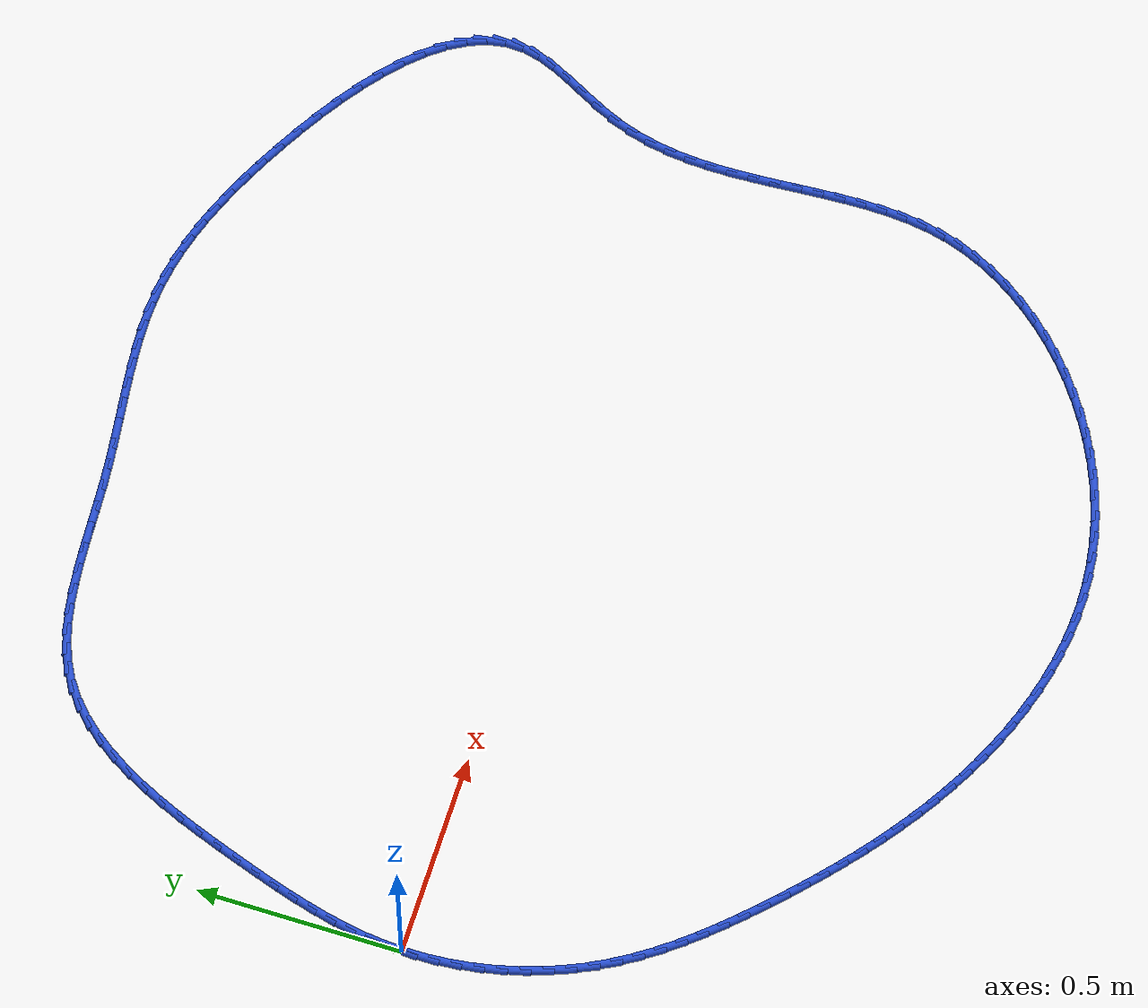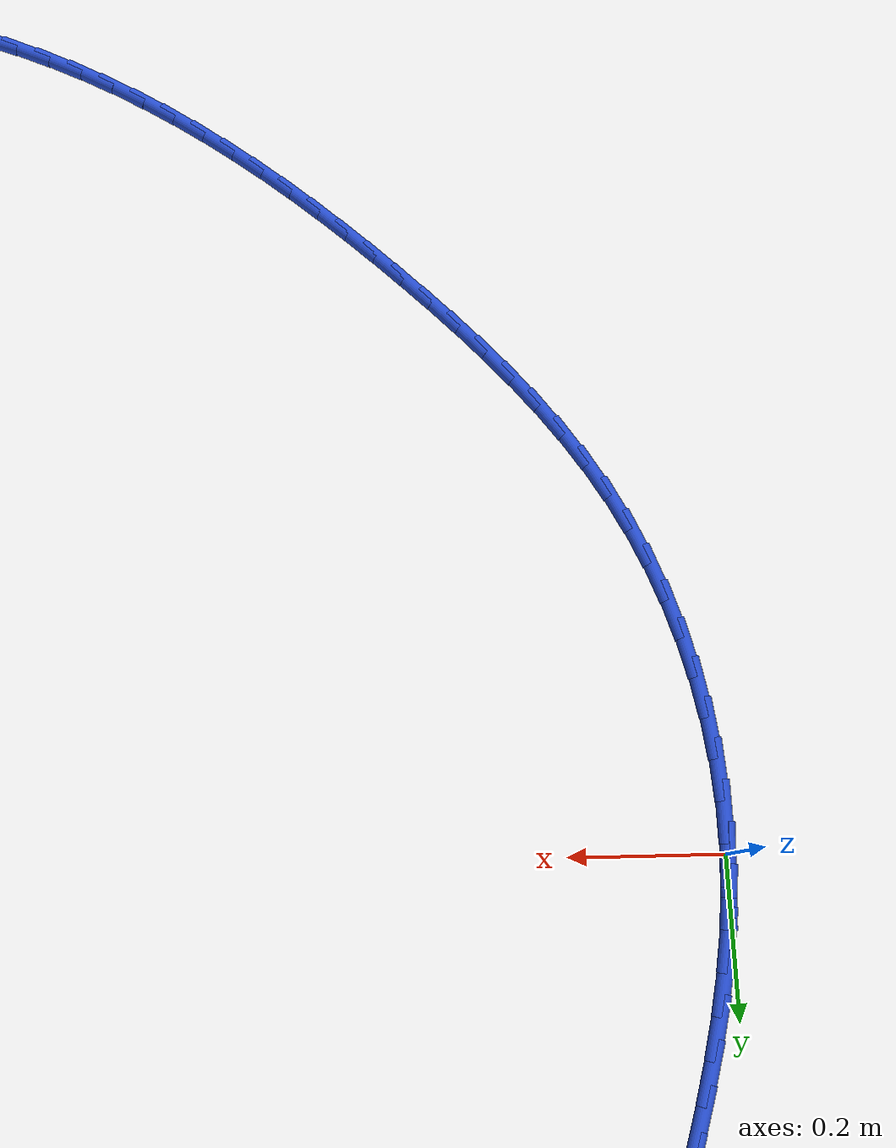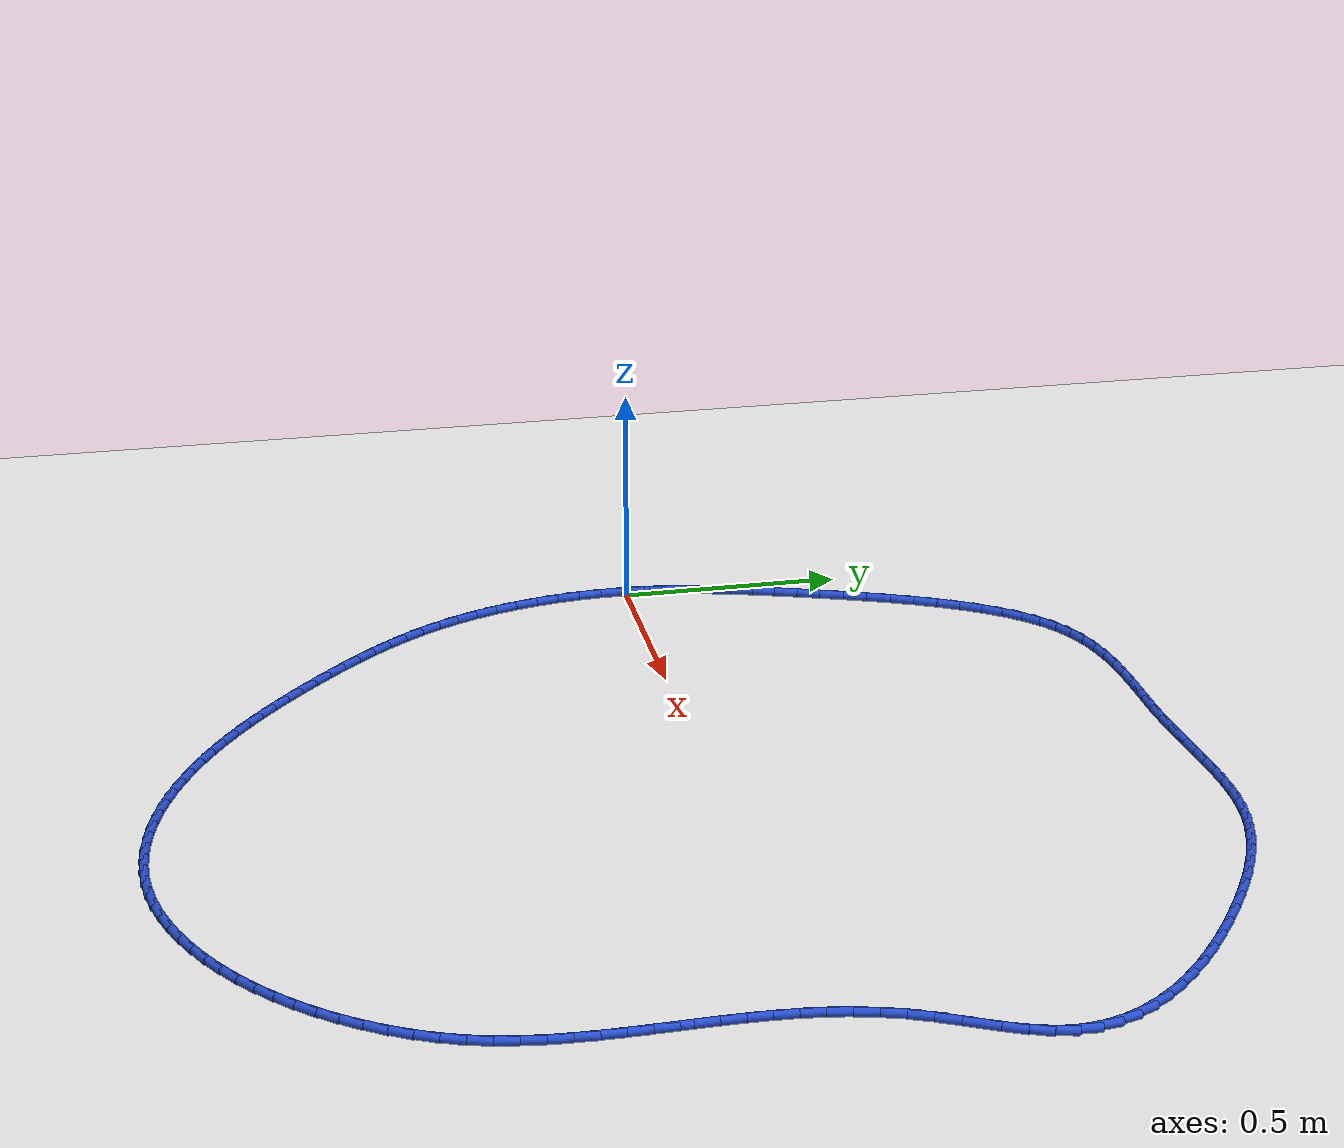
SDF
<sdf version="1.6">
 <world name="default">
  <light name="sun" type="directional">
   <pose>0 0 10 0 -0 0</pose>
   <diffuse>0.8 0.8 0.8 1</diffuse>
   <specular>0.2 0.2 0.2 1</specular>
   <attenuation>
    <range>1000</range>
    <constant>0.9</constant>
    <linear>0.01</linear>
    <quadratic>0.001</quadratic>
   </attenuation>
   <direction>-0.5 0.1 -0.9</direction>
  </light>
  <model name="ground_plane">
   <static>1</static>
   <link name="link">
    <collision name="collision">
     <geometry><plane><normal>0 0 1</normal><size>100 100</size></plane></geometry>
     <surface><friction><ode><mu>100</mu><mu2>50</mu2></ode></friction></surface>
    </collision>
    <visual name="visual">
     <cast_shadows>0</cast_shadows>
     <geometry><plane><normal>0 0 1</normal><size>100 100</size></plane></geometry>
     <material>
      <script><uri>file://media/materials/scripts/gazebo.material</uri><name>Gazebo/WhiteGlow</name></script>
     </material>
    </visual>
   </link>
  </model>
  <gravity>0 0 -9.8</gravity>
  <magnetic_field>6e-06 2.3e-05 -4.2e-05</magnetic_field>
  <atmosphere type="adiabatic"/>
  <physics name="default_physics" default="0" type="ode">
   <max_step_size>0.001</max_step_size>
   <real_time_factor>1</real_time_factor>
   <real_time_update_rate>1000</real_time_update_rate>
  </physics>
  <scene><ambient>0.4 0.4 0.4 1</ambient><background>0.7 0.7 0.7 1</background><shadows>1</shadows></scene>
  <spherical_coordinates>
   <surface_model>EARTH_WGS84</surface_model>
   <latitude_deg>0</latitude_deg>
   <longitude_deg>0</longitude_deg>
   <elevation>0</elevation>
   <heading_deg>0</heading_deg>
  </spherical_coordinates>
  <model name="line">
   <link name="link_0">
    <pose>1.734723475976807e-17 -1.5265566588595902e-16 0.01 0 1.57 1.5107257477533145</pose>
    <collision name="collision">
     <geometry><cylinder><radius>0.01</radius><length>0.08</length></cylinder></geometry>
    </collision>
    <visual name="visual">
     <material>
      <script><name>Gazebo/Blue</name><uri>file://media/materials/scripts/gazebo.material</uri></script>
     </material>
     <geometry><cylinder><radius>0.01</radius><length>0.08</length></cylinder></geometry>
    </visual>
   </link>
   <link name="link_1">
    <pose>0.0030970636344004538 0.0514950506932398 0.01 0 1.57 1.4526678016341241</pose>
    <collision name="collision">
     <geometry><cylinder><radius>0.01</radius><length>0.08</length></cylinder></geometry>
    </collision>
    <visual name="visual">
     <material>
      <script><name>Gazebo/Blue</name><uri>file://media/materials/scripts/gazebo.material</uri></script>
     </material>
     <geometry><cylinder><radius>0.01</radius><length>0.08</length></cylinder></geometry>
    </visual>
   </link>
   <link name="link_2">
    <pose>0.009151567106093004 0.10250995173038797 0.01 0 1.57 1.4008432162956856</pose>
    <collision name="collision">
     <geometry><cylinder><radius>0.01</radius><length>0.08</length></cylinder></geometry>
    </collision>
    <visual name="visual">
     <material>
      <script><name>Gazebo/Blue</name><uri>file://media/materials/scripts/gazebo.material</uri></script>
     </material>
     <geometry><cylinder><radius>0.01</radius><length>0.08</length></cylinder></geometry>
    </visual>
   </link>
   <link name="link_3">
    <pose>0.017853275384806383 0.15321668054593046 0.01 0 1.57 1.3558845297584416</pose>
    <collision name="collision">
     <geometry><cylinder><radius>0.01</radius><length>0.08</length></cylinder></geometry>
    </collision>
    <visual name="visual">
     <material>
      <script><name>Gazebo/Blue</name><uri>file://media/materials/scripts/gazebo.material</uri></script>
     </material>
     <geometry><cylinder><radius>0.01</radius><length>0.08</length></cylinder></geometry>
    </visual>
   </link>
   <link name="link_4">
    <pose>0.02889195344026932 0.2037872145743534 0.01 0 1.57 1.3181361157823994</pose>
    <collision name="collision">
     <geometry><cylinder><radius>0.01</radius><length>0.08</length></cylinder></geometry>
    </collision>
    <visual name="visual">
     <material>
      <script><name>Gazebo/Blue</name><uri>file://media/materials/scripts/gazebo.material</uri></script>
     </material>
     <geometry><cylinder><radius>0.01</radius><length>0.08</length></cylinder></geometry>
    </visual>
   </link>
   <link name="link_5">
    <pose>0.04195736624221055 0.2543935312501429 0.01 0 1.57 1.2877071524294774</pose>
    <collision name="collision">
     <geometry><cylinder><radius>0.01</radius><length>0.08</length></cylinder></geometry>
    </collision>
    <visual name="visual">
     <material>
      <script><name>Gazebo/Blue</name><uri>file://media/materials/scripts/gazebo.material</uri></script>
     </material>
     <geometry><cylinder><radius>0.01</radius><length>0.08</length></cylinder></geometry>
    </visual>
   </link>
   <link name="link_6">
    <pose>0.05673927876035881 0.30520760800778535 0.01 0 1.57 1.264531891017261</pose>
    <collision name="collision">
     <geometry><cylinder><radius>0.01</radius><length>0.08</length></cylinder></geometry>
    </collision>
    <visual name="visual">
     <material>
      <script><name>Gazebo/Blue</name><uri>file://media/materials/scripts/gazebo.material</uri></script>
     </material>
     <geometry><cylinder><radius>0.01</radius><length>0.08</length></cylinder></geometry>
    </visual>
   </link>
   <link name="link_7">
    <pose>0.0729274559644428 0.3564014222817665 0.01 0 1.57 1.2484250278614968</pose>
    <collision name="collision">
     <geometry><cylinder><radius>0.01</radius><length>0.08</length></cylinder></geometry>
    </collision>
    <visual name="visual">
     <material>
      <script><name>Gazebo/Blue</name><uri>file://media/materials/scripts/gazebo.material</uri></script>
     </material>
     <geometry><cylinder><radius>0.01</radius><length>0.08</length></cylinder></geometry>
    </visual>
   </link>
   <link name="link_8">
    <pose>0.09021166282419128 0.4081469515065728 0.01 0 1.57 1.2388290954331571</pose>
    <collision name="collision">
     <geometry><cylinder><radius>0.01</radius><length>0.08</length></cylinder></geometry>
    </collision>
    <visual name="visual">
     <material>
      <script><name>Gazebo/Blue</name><uri>file://media/materials/scripts/gazebo.material</uri></script>
     </material>
     <geometry><cylinder><radius>0.01</radius><length>0.08</length></cylinder></geometry>
    </visual>
   </link>
   <link name="link_9">
    <pose>0.10829365370096712 0.4606004233760592 0.01 0 1.57 1.2289346282761369</pose>
    <collision name="collision">
     <geometry><cylinder><radius>0.01</radius><length>0.08</length></cylinder></geometry>
    </collision>
    <visual name="visual">
     <material>
      <script><name>Gazebo/Blue</name><uri>file://media/materials/scripts/gazebo.material</uri></script>
     </material>
     <geometry><cylinder><radius>0.01</radius><length>0.08</length></cylinder></geometry>
    </visual>
   </link>
   <link name="link_10">
    <pose>0.12714139057040721 0.5135683646979344 0.01 0 1.57 1.212229698128397</pose>
    <collision name="collision">
     <geometry><cylinder><radius>0.01</radius><length>0.08</length></cylinder></geometry>
    </collision>
    <visual name="visual">
     <material>
      <script><name>Gazebo/Blue</name><uri>file://media/materials/scripts/gazebo.material</uri></script>
     </material>
     <geometry><cylinder><radius>0.01</radius><length>0.08</length></cylinder></geometry>
    </visual>
   </link>
   <link name="link_11">
    <pose>0.1469838439929107 0.566514431045243 0.01 0 1.57 1.188189695460614</pose>
    <collision name="collision">
     <geometry><cylinder><radius>0.01</radius><length>0.08</length></cylinder></geometry>
    </collision>
    <visual name="visual">
     <material>
      <script><name>Gazebo/Blue</name><uri>file://media/materials/scripts/gazebo.material</uri></script>
     </material>
     <geometry><cylinder><radius>0.01</radius><length>0.08</length></cylinder></geometry>
    </visual>
   </link>
   <link name="link_12">
    <pose>0.16806093398780694 0.6188878943472663 0.01 0 1.57 1.1562634860405452</pose>
    <collision name="collision">
     <geometry><cylinder><radius>0.01</radius><length>0.08</length></cylinder></geometry>
    </collision>
    <visual name="visual">
     <material>
      <script><name>Gazebo/Blue</name><uri>file://media/materials/scripts/gazebo.material</uri></script>
     </material>
     <geometry><cylinder><radius>0.01</radius><length>0.08</length></cylinder></geometry>
    </visual>
   </link>
   <link name="link_13">
    <pose>0.19061258057442523 0.6701380265332856 0.01 0 1.57 1.1156061505791022</pose>
    <collision name="collision">
     <geometry><cylinder><radius>0.01</radius><length>0.08</length></cylinder></geometry>
    </collision>
    <visual name="visual">
     <material>
      <script><name>Gazebo/Blue</name><uri>file://media/materials/scripts/gazebo.material</uri></script>
     </material>
     <geometry><cylinder><radius>0.01</radius><length>0.08</length></cylinder></geometry>
    </visual>
   </link>
   <link name="link_14">
    <pose>0.21487870377209484 0.719714099532582 0.01 0 1.57 1.0650827127361802</pose>
    <collision name="collision">
     <geometry><cylinder><radius>0.01</radius><length>0.08</length></cylinder></geometry>
    </collision>
    <visual name="visual">
     <material>
      <script><name>Gazebo/Blue</name><uri>file://media/materials/scripts/gazebo.material</uri></script>
     </material>
     <geometry><cylinder><radius>0.01</radius><length>0.08</length></cylinder></geometry>
    </visual>
   </link>
   <link name="link_15">
    <pose>0.24109922360014524 0.7670653852744374 0.01 0 1.57 1.0032940689407928</pose>
    <collision name="collision">
     <geometry><cylinder><radius>0.01</radius><length>0.08</length></cylinder></geometry>
    </collision>
    <visual name="visual">
     <material>
      <script><name>Gazebo/Blue</name><uri>file://media/materials/scripts/gazebo.material</uri></script>
     </material>
     <geometry><cylinder><radius>0.01</radius><length>0.08</length></cylinder></geometry>
    </visual>
   </link>
   <link name="link_16">
    <pose>0.2695140600779057 0.8116411556881329 0.01 0 1.57 0.9286630868771775</pose>
    <collision name="collision">
     <geometry><cylinder><radius>0.01</radius><length>0.08</length></cylinder></geometry>
    </collision>
    <visual name="visual">
     <material>
      <script><name>Gazebo/Blue</name><uri>file://media/materials/scripts/gazebo.material</uri></script>
     </material>
     <geometry><cylinder><radius>0.01</radius><length>0.08</length></cylinder></geometry>
    </visual>
   </link>
   <link name="link_17">
    <pose>0.3003631332247054 0.85289068270295 0.01 0 1.57 0.8396404537288016</pose>
    <collision name="collision">
     <geometry><cylinder><radius>0.01</radius><length>0.08</length></cylinder></geometry>
    </collision>
    <visual name="visual">
     <material>
      <script><name>Gazebo/Blue</name><uri>file://media/materials/scripts/gazebo.material</uri></script>
     </material>
     <geometry><cylinder><radius>0.01</radius><length>0.08</length></cylinder></geometry>
    </visual>
   </link>
   <link name="link_18">
    <pose>0.33388636305987385 0.8902632382481699 0.01 0 1.57 0.735104179857981</pose>
    <collision name="collision">
     <geometry><cylinder><radius>0.01</radius><length>0.08</length></cylinder></geometry>
    </collision>
    <visual name="visual">
     <material>
      <script><name>Gazebo/Blue</name><uri>file://media/materials/scripts/gazebo.material</uri></script>
     </material>
     <geometry><cylinder><radius>0.01</radius><length>0.08</length></cylinder></geometry>
    </visual>
   </link>
   <link name="link_19">
    <pose>0.3703236696027404 0.9232080942530744 0.01 0 1.57 0.6149937343319832</pose>
    <collision name="collision">
     <geometry><cylinder><radius>0.01</radius><length>0.08</length></cylinder></geometry>
    </collision>
    <visual name="visual">
     <material>
      <script><name>Gazebo/Blue</name><uri>file://media/materials/scripts/gazebo.material</uri></script>
     </material>
     <geometry><cylinder><radius>0.01</radius><length>0.08</length></cylinder></geometry>
    </visual>
   </link>
   <link name="link_20">
    <pose>0.4099149728726343 0.9511745226469445 0.01 0 1.57 0.48525182381063026</pose>
    <collision name="collision">
     <geometry><cylinder><radius>0.01</radius><length>0.08</length></cylinder></geometry>
    </collision>
    <visual name="visual">
     <material>
      <script><name>Gazebo/Blue</name><uri>file://media/materials/scripts/gazebo.material</uri></script>
     </material>
     <geometry><cylinder><radius>0.01</radius><length>0.08</length></cylinder></geometry>
    </visual>
   </link>
   <link name="link_21">
    <pose>0.4528073591992297 0.9737918693611268 0.01 0 1.57 0.36862551900560253</pose>
    <collision name="collision">
     <geometry><cylinder><radius>0.01</radius><length>0.08</length></cylinder></geometry>
    </collision>
    <visual name="visual">
     <material>
      <script><name>Gazebo/Blue</name><uri>file://media/materials/scripts/gazebo.material</uri></script>
     </material>
     <geometry><cylinder><radius>0.01</radius><length>0.08</length></cylinder></geometry>
    </visual>
   </link>
   <link name="link_22">
    <pose>0.498716731414702 0.9915258678314155 0.01 0 1.57 0.2725160425857033</pose>
    <collision name="collision">
     <geometry><cylinder><radius>0.01</radius><length>0.08</length></cylinder></geometry>
    </collision>
    <visual name="visual">
     <material>
      <script><name>Gazebo/Blue</name><uri>file://media/materials/scripts/gazebo.material</uri></script>
     </material>
     <geometry><cylinder><radius>0.01</radius><length>0.08</length></cylinder></geometry>
    </visual>
   </link>
   <link name="link_23">
    <pose>0.5472338986674423 1.0050849017680448 0.01 0 1.57 0.1964346536146504</pose>
    <collision name="collision">
     <geometry><cylinder><radius>0.01</radius><length>0.08</length></cylinder></geometry>
    </collision>
    <visual name="visual">
     <material>
      <script><name>Gazebo/Blue</name><uri>file://media/materials/scripts/gazebo.material</uri></script>
     </material>
     <geometry><cylinder><radius>0.01</radius><length>0.08</length></cylinder></geometry>
    </visual>
   </link>
   <link name="link_24">
    <pose>0.5979496567933027 1.0151773807042255 0.01 0 1.57 0.1387898288342589</pose>
    <collision name="collision">
     <geometry><cylinder><radius>0.01</radius><length>0.08</length></cylinder></geometry>
    </collision>
    <visual name="visual">
     <material>
      <script><name>Gazebo/Blue</name><uri>file://media/materials/scripts/gazebo.material</uri></script>
     </material>
     <geometry><cylinder><radius>0.01</radius><length>0.08</length></cylinder></geometry>
    </visual>
   </link>
   <link name="link_25">
    <pose>0.6504548016281351 1.0225117141731677 0.01 0 1.57 0.09775856532160106</pose>
    <collision name="collision">
     <geometry><cylinder><radius>0.01</radius><length>0.08</length></cylinder></geometry>
    </collision>
    <visual name="visual">
     <material>
      <script><name>Gazebo/Blue</name><uri>file://media/materials/scripts/gazebo.material</uri></script>
     </material>
     <geometry><cylinder><radius>0.01</radius><length>0.08</length></cylinder></geometry>
    </visual>
   </link>
   <link name="link_26">
    <pose>0.7043401290077916 1.0277963117080828 0.01 0 1.57 0.07176021230202217</pose>
    <collision name="collision">
     <geometry><cylinder><radius>0.01</radius><length>0.08</length></cylinder></geometry>
    </collision>
    <visual name="visual">
     <material>
      <script><name>Gazebo/Blue</name><uri>file://media/materials/scripts/gazebo.material</uri></script>
     </material>
     <geometry><cylinder><radius>0.01</radius><length>0.08</length></cylinder></geometry>
    </visual>
   </link>
   <link name="link_27">
    <pose>0.7591964347681244 1.0317395828421805 0.01 0 1.57 0.05966329705790118</pose>
    <collision name="collision">
     <geometry><cylinder><radius>0.01</radius><length>0.08</length></cylinder></geometry>
    </collision>
    <visual name="visual">
     <material>
      <script><name>Gazebo/Blue</name><uri>file://media/materials/scripts/gazebo.material</uri></script>
     </material>
     <geometry><cylinder><radius>0.01</radius><length>0.08</length></cylinder></geometry>
    </visual>
   </link>
   <link name="link_28">
    <pose>0.8146145147449855 1.0350499371086717 0.01 0 1.57 0.060853462610211406</pose>
    <collision name="collision">
     <geometry><cylinder><radius>0.01</radius><length>0.08</length></cylinder></geometry>
    </collision>
    <visual name="visual">
     <material>
      <script><name>Gazebo/Blue</name><uri>file://media/materials/scripts/gazebo.material</uri></script>
     </material>
     <geometry><cylinder><radius>0.01</radius><length>0.08</length></cylinder></geometry>
    </visual>
   </link>
   <link name="link_29">
    <pose>0.8701851647742274 1.0384357840407672 0.01 0 1.57 0.0752409222329639</pose>
    <collision name="collision">
     <geometry><cylinder><radius>0.01</radius><length>0.08</length></cylinder></geometry>
    </collision>
    <visual name="visual">
     <material>
      <script><name>Gazebo/Blue</name><uri>file://media/materials/scripts/gazebo.material</uri></script>
     </material>
     <geometry><cylinder><radius>0.01</radius><length>0.08</length></cylinder></geometry>
    </visual>
   </link>
   <link name="link_30">
    <pose>0.9254991806917017 1.0426055331716773 0.01 0 1.57 0.09961316940062143</pose>
    <collision name="collision">
     <geometry><cylinder><radius>0.01</radius><length>0.08</length></cylinder></geometry>
    </collision>
    <visual name="visual">
     <material>
      <script><name>Gazebo/Blue</name><uri>file://media/materials/scripts/gazebo.material</uri></script>
     </material>
     <geometry><cylinder><radius>0.01</radius><length>0.08</length></cylinder></geometry>
    </visual>
   </link>
   <link name="link_31">
    <pose>0.9802142159601525 1.0480739705986826 0.01 0 1.57 0.11894641381810851</pose>
    <collision name="collision">
     <geometry><cylinder><radius>0.01</radius><length>0.08</length></cylinder></geometry>
    </collision>
    <visual name="visual">
     <material>
      <script><name>Gazebo/Blue</name><uri>file://media/materials/scripts/gazebo.material</uri></script>
     </material>
     <geometry><cylinder><radius>0.01</radius><length>0.08</length></cylinder></geometry>
    </visual>
   </link>
   <link name="link_32">
    <pose>1.0342715806587541 1.054534396954338 0.01 0 1.57 0.12897646220863757</pose>
    <collision name="collision">
     <geometry><cylinder><radius>0.01</radius><length>0.08</length></cylinder></geometry>
    </collision>
    <visual name="visual">
     <material>
      <script><name>Gazebo/Blue</name><uri>file://media/materials/scripts/gazebo.material</uri></script>
     </material>
     <geometry><cylinder><radius>0.01</radius><length>0.08</length></cylinder></geometry>
    </visual>
   </link>
   <link name="link_33">
    <pose>1.0876877986815856 1.0614622894462864 0.01 0 1.57 0.1294226590567539</pose>
    <collision name="collision">
     <geometry><cylinder><radius>0.01</radius><length>0.08</length></cylinder></geometry>
    </collision>
    <visual name="visual">
     <material>
      <script><name>Gazebo/Blue</name><uri>file://media/materials/scripts/gazebo.material</uri></script>
     </material>
     <geometry><cylinder><radius>0.01</radius><length>0.08</length></cylinder></geometry>
    </visual>
   </link>
   <link name="link_34">
    <pose>1.1404793944594787 1.0683331237277016 0.01 0 1.57 0.11994333644022806</pose>
    <collision name="collision">
     <geometry><cylinder><radius>0.01</radius><length>0.08</length></cylinder></geometry>
    </collision>
    <visual name="visual">
     <material>
      <script><name>Gazebo/Blue</name><uri>file://media/materials/scripts/gazebo.material</uri></script>
     </material>
     <geometry><cylinder><radius>0.01</radius><length>0.08</length></cylinder></geometry>
    </visual>
   </link>
   <link name="link_35">
    <pose>1.1926628924232654 1.0746223754517572 0.01 0 1.57 0.10012830035620568</pose>
    <collision name="collision">
     <geometry><cylinder><radius>0.01</radius><length>0.08</length></cylinder></geometry>
    </collision>
    <visual name="visual">
     <material>
      <script><name>Gazebo/Blue</name><uri>file://media/materials/scripts/gazebo.material</uri></script>
     </material>
     <geometry><cylinder><radius>0.01</radius><length>0.08</length></cylinder></geometry>
    </visual>
   </link>
   <link name="link_36">
    <pose>1.2442548170037773 1.0798055202716272 0.01 0 1.57 0.06952186385192642</pose>
    <collision name="collision">
     <geometry><cylinder><radius>0.01</radius><length>0.08</length></cylinder></geometry>
    </collision>
    <visual name="visual">
     <material>
      <script><name>Gazebo/Blue</name><uri>file://media/materials/scripts/gazebo.material</uri></script>
     </material>
     <geometry><cylinder><radius>0.01</radius><length>0.08</length></cylinder></geometry>
    </visual>
   </link>
   <link name="link_37">
    <pose>1.2952716926318477 1.0833580338404858 0.01 0 1.57 0.02768621813346353</pose>
    <collision name="collision">
     <geometry><cylinder><radius>0.01</radius><length>0.08</length></cylinder></geometry>
    </collision>
    <visual name="visual">
     <material>
      <script><name>Gazebo/Blue</name><uri>file://media/materials/scripts/gazebo.material</uri></script>
     </material>
     <geometry><cylinder><radius>0.01</radius><length>0.08</length></cylinder></geometry>
    </visual>
   </link>
   <link name="link_38">
    <pose>1.3457300437383077 1.084755391811507 0.01 0 1.57 -0.025683768372066793</pose>
    <collision name="collision">
     <geometry><cylinder><radius>0.01</radius><length>0.08</length></cylinder></geometry>
    </collision>
    <visual name="visual">
     <material>
      <script><name>Gazebo/Blue</name><uri>file://media/materials/scripts/gazebo.material</uri></script>
     </material>
     <geometry><cylinder><radius>0.01</radius><length>0.08</length></cylinder></geometry>
    </visual>
   </link>
   <link name="link_39">
    <pose>1.3956463947539903 1.083473069837864 0.01 0 1.57 -0.08882800558701162</pose>
    <collision name="collision">
     <geometry><cylinder><radius>0.01</radius><length>0.08</length></cylinder></geometry>
    </collision>
    <visual name="visual">
     <material>
      <script><name>Gazebo/Blue</name><uri>file://media/materials/scripts/gazebo.material</uri></script>
     </material>
     <geometry><cylinder><radius>0.01</radius><length>0.08</length></cylinder></geometry>
    </visual>
   </link>
   <link name="link_40">
    <pose>1.4450603351671718 1.0790721469339877 0.01 0 1.57 -0.15240149437180758</pose>
    <collision name="collision">
     <geometry><cylinder><radius>0.01</radius><length>0.08</length></cylinder></geometry>
    </collision>
    <visual name="visual">
     <material>
      <script><name>Gazebo/Blue</name><uri>file://media/materials/scripts/gazebo.material</uri></script>
     </material>
     <geometry><cylinder><radius>0.01</radius><length>0.08</length></cylinder></geometry>
    </visual>
   </link>
   <link name="link_41">
    <pose>1.4941252770053866 1.0715361416408502 0.01 0 1.57 -0.21261719389894854</pose>
    <collision name="collision">
     <geometry><cylinder><radius>0.01</radius><length>0.08</length></cylinder></geometry>
    </collision>
    <visual name="visual">
     <material>
      <script><name>Gazebo/Blue</name><uri>file://media/materials/scripts/gazebo.material</uri></script>
     </material>
     <geometry><cylinder><radius>0.01</radius><length>0.08</length></cylinder></geometry>
    </visual>
   </link>
   <link name="link_42">
    <pose>1.5430296819341953 1.0609786552808371 0.01 0 1.57 -0.2685359937160583</pose>
    <collision name="collision">
     <geometry><cylinder><radius>0.01</radius><length>0.08</length></cylinder></geometry>
    </collision>
    <visual name="visual">
     <material>
      <script><name>Gazebo/Blue</name><uri>file://media/materials/scripts/gazebo.material</uri></script>
     </material>
     <geometry><cylinder><radius>0.01</radius><length>0.08</length></cylinder></geometry>
    </visual>
   </link>
   <link name="link_43">
    <pose>1.5919620213701002 1.0475133253658537 0.01 0 1.57 -0.3194895659780439</pose>
    <collision name="collision">
     <geometry><cylinder><radius>0.01</radius><length>0.08</length></cylinder></geometry>
    </collision>
    <visual name="visual">
     <material>
      <script><name>Gazebo/Blue</name><uri>file://media/materials/scripts/gazebo.material</uri></script>
     </material>
     <geometry><cylinder><radius>0.01</radius><length>0.08</length></cylinder></geometry>
    </visual>
   </link>
   <link name="link_44">
    <pose>1.6411107667296034 1.0312537894078044 0.01 0 1.57 -0.3650805087860899</pose>
    <collision name="collision">
     <geometry><cylinder><radius>0.01</radius><length>0.08</length></cylinder></geometry>
    </collision>
    <visual name="visual">
     <material>
      <script><name>Gazebo/Blue</name><uri>file://media/materials/scripts/gazebo.material</uri></script>
     </material>
     <geometry><cylinder><radius>0.01</radius><length>0.08</length></cylinder></geometry>
    </visual>
   </link>
   <link name="link_45">
    <pose>1.6906643894292066 1.0123136849185939 0.01 0 1.57 -0.40515248707323426</pose>
    <collision name="collision">
     <geometry><cylinder><radius>0.01</radius><length>0.08</length></cylinder></geometry>
    </collision>
    <visual name="visual">
     <material>
      <script><name>Gazebo/Blue</name><uri>file://media/materials/scripts/gazebo.material</uri></script>
     </material>
     <geometry><cylinder><radius>0.01</radius><length>0.08</length></cylinder></geometry>
    </visual>
   </link>
   <link name="link_46">
    <pose>1.7408113608854126 0.9908066494101267 0.01 0 1.57 -0.43974353550637707</pose>
    <collision name="collision">
     <geometry><cylinder><radius>0.01</radius><length>0.08</length></cylinder></geometry>
    </collision>
    <visual name="visual">
     <material>
      <script><name>Gazebo/Blue</name><uri>file://media/materials/scripts/gazebo.material</uri></script>
     </material>
     <geometry><cylinder><radius>0.01</radius><length>0.08</length></cylinder></geometry>
    </visual>
   </link>
   <link name="link_47">
    <pose>1.7917401525147227 0.966846320394308 0.01 0 1.57 -0.4690349263080847</pose>
    <collision name="collision">
     <geometry><cylinder><radius>0.01</radius><length>0.08</length></cylinder></geometry>
    </collision>
    <visual name="visual">
     <material>
      <script><name>Gazebo/Blue</name><uri>file://media/materials/scripts/gazebo.material</uri></script>
     </material>
     <geometry><cylinder><radius>0.01</radius><length>0.08</length></cylinder></geometry>
    </visual>
   </link>
   <link name="link_48">
    <pose>1.8436392357336393 0.9405463353830416 0.01 0 1.57 -0.4940879928433445</pose>
    <collision name="collision">
     <geometry><cylinder><radius>0.01</radius><length>0.08</length></cylinder></geometry>
    </collision>
    <visual name="visual">
     <material>
      <script><name>Gazebo/Blue</name><uri>file://media/materials/scripts/gazebo.material</uri></script>
     </material>
     <geometry><cylinder><radius>0.01</radius><length>0.08</length></cylinder></geometry>
    </visual>
   </link>
   <link name="link_49">
    <pose>1.8965959243383745 0.9120211785481052 0.01 0 1.57 -0.520793197811523</pose>
    <collision name="collision">
     <geometry><cylinder><radius>0.01</radius><length>0.08</length></cylinder></geometry>
    </collision>
    <visual name="visual">
     <material>
      <script><name>Gazebo/Blue</name><uri>file://media/materials/scripts/gazebo.material</uri></script>
     </material>
     <geometry><cylinder><radius>0.01</radius><length>0.08</length></cylinder></geometry>
    </visual>
   </link>
   <link name="link_50">
    <pose>1.9499939826631563 0.881391222565731 0.01 0 1.57 -0.5522450673170698</pose>
    <collision name="collision">
     <geometry><cylinder><radius>0.01</radius><length>0.08</length></cylinder></geometry>
    </collision>
    <visual name="visual">
     <material>
      <script><name>Gazebo/Blue</name><uri>file://media/materials/scripts/gazebo.material</uri></script>
     </material>
     <geometry><cylinder><radius>0.01</radius><length>0.08</length></cylinder></geometry>
    </visual>
   </link>
   <link name="link_51">
    <pose>2.002918296914024 0.8487793416351925 0.01 0 1.57 -0.5895416079618973</pose>
    <collision name="collision">
     <geometry><cylinder><radius>0.01</radius><length>0.08</length></cylinder></geometry>
    </collision>
    <visual name="visual">
     <material>
      <script><name>Gazebo/Blue</name><uri>file://media/materials/scripts/gazebo.material</uri></script>
     </material>
     <geometry><cylinder><radius>0.01</radius><length>0.08</length></cylinder></geometry>
    </visual>
   </link>
   <link name="link_52">
    <pose>2.054452662274408 0.8143084190873051 0.01 0 1.57 -0.6341527954027874</pose>
    <collision name="collision">
     <geometry><cylinder><radius>0.01</radius><length>0.08</length></cylinder></geometry>
    </collision>
    <visual name="visual">
     <material>
      <script><name>Gazebo/Blue</name><uri>file://media/materials/scripts/gazebo.material</uri></script>
     </material>
     <geometry><cylinder><radius>0.01</radius><length>0.08</length></cylinder></geometry>
    </visual>
   </link>
   <link name="link_53">
    <pose>2.1036808739277366 0.7781013382528841 0.01 0 1.57 -0.6880583402300781</pose>
    <collision name="collision">
     <geometry><cylinder><radius>0.01</radius><length>0.08</length></cylinder></geometry>
    </collision>
    <visual name="visual">
     <material>
      <script><name>Gazebo/Blue</name><uri>file://media/materials/scripts/gazebo.material</uri></script>
     </material>
     <geometry><cylinder><radius>0.01</radius><length>0.08</length></cylinder></geometry>
    </visual>
   </link>
   <link name="link_54">
    <pose>2.149686727057439 0.7402809824627444 0.01 0 1.57 -0.7539155387511322</pose>
    <collision name="collision">
     <geometry><cylinder><radius>0.01</radius><length>0.08</length></cylinder></geometry>
    </collision>
    <visual name="visual">
     <material>
      <script><name>Gazebo/Blue</name><uri>file://media/materials/scripts/gazebo.material</uri></script>
     </material>
     <geometry><cylinder><radius>0.01</radius><length>0.08</length></cylinder></geometry>
    </visual>
   </link>
   <link name="link_55">
    <pose>2.1915540168469447 0.7009702350477014 0.01 0 1.57 -0.8352432181044779</pose>
    <collision name="collision">
     <geometry><cylinder><radius>0.01</radius><length>0.08</length></cylinder></geometry>
    </collision>
    <visual name="visual">
     <material>
      <script><name>Gazebo/Blue</name><uri>file://media/materials/scripts/gazebo.material</uri></script>
     </material>
     <geometry><cylinder><radius>0.01</radius><length>0.08</length></cylinder></geometry>
    </visual>
   </link>
   <link name="link_56">
    <pose>2.228366538479681 0.6602919793385709 0.01 0 1.57 -0.9365274618492212</pose>
    <collision name="collision">
     <geometry><cylinder><radius>0.01</radius><length>0.08</length></cylinder></geometry>
    </collision>
    <visual name="visual">
     <material>
      <script><name>Gazebo/Blue</name><uri>file://media/materials/scripts/gazebo.material</uri></script>
     </material>
     <geometry><cylinder><radius>0.01</radius><length>0.08</length></cylinder></geometry>
    </visual>
   </link>
   <link name="link_57">
    <pose>2.25920808713908 0.6183690986661675 0.01 0 1.57 -1.062975729726447</pose>
    <collision name="collision">
     <geometry><cylinder><radius>0.01</radius><length>0.08</length></cylinder></geometry>
    </collision>
    <visual name="visual">
     <material>
      <script><name>Gazebo/Blue</name><uri>file://media/materials/scripts/gazebo.material</uri></script>
     </material>
     <geometry><cylinder><radius>0.01</radius><length>0.08</length></cylinder></geometry>
    </visual>
   </link>
   <link name="link_58">
    <pose>2.2831624580085683 0.5753244763613071 0.01 0 1.57 -1.2193172683430173</pose>
    <collision name="collision">
     <geometry><cylinder><radius>0.01</radius><length>0.08</length></cylinder></geometry>
    </collision>
    <visual name="visual">
     <material>
      <script><name>Gazebo/Blue</name><uri>file://media/materials/scripts/gazebo.material</uri></script>
     </material>
     <geometry><cylinder><radius>0.01</radius><length>0.08</length></cylinder></geometry>
    </visual>
   </link>
   <link name="link_59">
    <pose>2.2993134462715763 0.5312809957548047 0.01 0 1.57 -1.4068430009241806</pose>
    <collision name="collision">
     <geometry><cylinder><radius>0.01</radius><length>0.08</length></cylinder></geometry>
    </collision>
    <visual name="visual">
     <material>
      <script><name>Gazebo/Blue</name><uri>file://media/materials/scripts/gazebo.material</uri></script>
     </material>
     <geometry><cylinder><radius>0.01</radius><length>0.08</length></cylinder></geometry>
    </visual>
   </link>
   <link name="link_60">
    <pose>2.3067448471115313 0.4863615401774759 0.01 0 1.57 1.5225770073862193</pose>
    <collision name="collision">
     <geometry><cylinder><radius>0.01</radius><length>0.08</length></cylinder></geometry>
    </collision>
    <visual name="visual">
     <material>
      <script><name>Gazebo/Blue</name><uri>file://media/materials/scripts/gazebo.material</uri></script>
     </material>
     <geometry><cylinder><radius>0.01</radius><length>0.08</length></cylinder></geometry>
    </visual>
   </link>
   <link name="link_61">
    <pose>2.3045408387234247 0.4406889763943976 0.01 0 1.57 1.3181266325658358</pose>
    <collision name="collision">
     <geometry><cylinder><radius>0.01</radius><length>0.08</length></cylinder></geometry>
    </collision>
    <visual name="visual">
     <material>
      <script><name>Gazebo/Blue</name><uri>file://media/materials/scripts/gazebo.material</uri></script>
     </material>
     <geometry><cylinder><radius>0.01</radius><length>0.08</length></cylinder></geometry>
    </visual>
   </link>
   <link name="link_62">
    <pose>2.292577187796854 0.39435193396003226 0.01 0 1.57 1.1796492211141394</pose>
    <collision name="collision">
     <geometry><cylinder><radius>0.01</radius><length>0.08</length></cylinder></geometry>
    </collision>
    <visual name="visual">
     <material>
      <script><name>Gazebo/Blue</name><uri>file://media/materials/scripts/gazebo.material</uri></script>
     </material>
     <geometry><cylinder><radius>0.01</radius><length>0.08</length></cylinder></geometry>
    </visual>
   </link>
   <link name="link_63">
    <pose>2.2731866521032957 0.34733277443514937 0.01 0 1.57 1.1048114834860978</pose>
    <collision name="collision">
     <geometry><cylinder><radius>0.01</radius><length>0.08</length></cylinder></geometry>
    </collision>
    <visual name="visual">
     <material>
      <script><name>Gazebo/Blue</name><uri>file://media/materials/scripts/gazebo.material</uri></script>
     </material>
     <geometry><cylinder><radius>0.01</radius><length>0.08</length></cylinder></geometry>
    </visual>
   </link>
   <link name="link_64">
    <pose>2.249177279769019 0.2995933024673109 0.01 0 1.57 1.081568553699858</pose>
    <collision name="collision">
     <geometry><cylinder><radius>0.01</radius><length>0.08</length></cylinder></geometry>
    </collision>
    <visual name="visual">
     <material>
      <script><name>Gazebo/Blue</name><uri>file://media/materials/scripts/gazebo.material</uri></script>
     </material>
     <geometry><cylinder><radius>0.01</radius><length>0.08</length></cylinder></geometry>
    </visual>
   </link>
   <link name="link_65">
    <pose>2.223357118920297 0.2510953227040785 0.01 0 1.57 1.104303630966705</pose>
    <collision name="collision">
     <geometry><cylinder><radius>0.01</radius><length>0.08</length></cylinder></geometry>
    </collision>
    <visual name="visual">
     <material>
      <script><name>Gazebo/Blue</name><uri>file://media/materials/scripts/gazebo.material</uri></script>
     </material>
     <geometry><cylinder><radius>0.01</radius><length>0.08</length></cylinder></geometry>
    </visual>
   </link>
   <link name="link_66">
    <pose>2.1985342176833997 0.20180063979301288 0.01 0 1.57 1.1731220031187062</pose>
    <collision name="collision">
     <geometry><cylinder><radius>0.01</radius><length>0.08</length></cylinder></geometry>
    </collision>
    <visual name="visual">
     <material>
      <script><name>Gazebo/Blue</name><uri>file://media/materials/scripts/gazebo.material</uri></script>
     </material>
     <geometry><cylinder><radius>0.01</radius><length>0.08</length></cylinder></geometry>
    </visual>
   </link>
   <link name="link_67">
    <pose>2.177477769069307 0.15167274376294562 0.01 0 1.57 1.2671250671486205</pose>
    <collision name="collision">
     <geometry><cylinder><radius>0.01</radius><length>0.08</length></cylinder></geometry>
    </collision>
    <visual name="visual">
     <material>
      <script><name>Gazebo/Blue</name><uri>file://media/materials/scripts/gazebo.material</uri></script>
     </material>
     <geometry><cylinder><radius>0.01</radius><length>0.08</length></cylinder></geometry>
    </visual>
   </link>
   <link name="link_68">
    <pose>2.1615165604315734 0.10073760374480074 0.01 0 1.57 1.354086795164533</pose>
    <collision name="collision">
     <geometry><cylinder><radius>0.01</radius><length>0.08</length></cylinder></geometry>
    </collision>
    <visual name="visual">
     <material>
      <script><name>Gazebo/Blue</name><uri>file://media/materials/scripts/gazebo.material</uri></script>
     </material>
     <geometry><cylinder><radius>0.01</radius><length>0.08</length></cylinder></geometry>
    </visual>
   </link>
   <link name="link_69">
    <pose>2.150147807128575 0.04910063522066866 0.01 0 1.57 1.4300926281372786</pose>
    <collision name="collision">
     <geometry><cylinder><radius>0.01</radius><length>0.08</length></cylinder></geometry>
    </collision>
    <visual name="visual">
     <material>
      <script><name>Gazebo/Blue</name><uri>file://media/materials/scripts/gazebo.material</uri></script>
     </material>
     <geometry><cylinder><radius>0.01</radius><length>0.08</length></cylinder></geometry>
    </visual>
   </link>
   <link name="link_70">
    <pose>2.1427502178637186 -0.0031276059772412618 0.01 0 1.57 1.4941530411305144</pose>
    <collision name="collision">
     <geometry><cylinder><radius>0.01</radius><length>0.08</length></cylinder></geometry>
    </collision>
    <visual name="visual">
     <material>
      <script><name>Gazebo/Blue</name><uri>file://media/materials/scripts/gazebo.material</uri></script>
     </material>
     <geometry><cylinder><radius>0.01</radius><length>0.08</length></cylinder></geometry>
    </visual>
   </link>
   <link name="link_71">
    <pose>2.1387025013404113 -0.05583656401671815 0.01 0 1.57 1.545949200057749</pose>
    <collision name="collision">
     <geometry><cylinder><radius>0.01</radius><length>0.08</length></cylinder></geometry>
    </collision>
    <visual name="visual">
     <material>
      <script><name>Gazebo/Blue</name><uri>file://media/materials/scripts/gazebo.material</uri></script>
     </material>
     <geometry><cylinder><radius>0.01</radius><length>0.08</length></cylinder></geometry>
    </visual>
   </link>
   <link name="link_72">
    <pose>2.1373833662620587 -0.10891568306555233 0.01 0 1.57 -1.556020988119271</pose>
    <collision name="collision">
     <geometry><cylinder><radius>0.01</radius><length>0.08</length></cylinder></geometry>
    </collision>
    <visual name="visual">
     <material>
      <script><name>Gazebo/Blue</name><uri>file://media/materials/scripts/gazebo.material</uri></script>
     </material>
     <geometry><cylinder><radius>0.01</radius><length>0.08</length></cylinder></geometry>
    </visual>
   </link>
   <link name="link_73">
    <pose>2.138171521332069 -0.1622544072915345 0.01 0 1.57 -1.5283046523151043</pose>
    <collision name="collision">
     <geometry><cylinder><radius>0.01</radius><length>0.08</length></cylinder></geometry>
    </collision>
    <visual name="visual">
     <material>
      <script><name>Gazebo/Blue</name><uri>file://media/materials/scripts/gazebo.material</uri></script>
     </material>
     <geometry><cylinder><radius>0.01</radius><length>0.08</length></cylinder></geometry>
    </visual>
   </link>
   <link name="link_74">
    <pose>2.140445675253847 -0.2157421808624529 0.01 0 1.57 -1.5122218912454404</pose>
    <collision name="collision">
     <geometry><cylinder><radius>0.01</radius><length>0.08</length></cylinder></geometry>
    </collision>
    <visual name="visual">
     <material>
      <script><name>Gazebo/Blue</name><uri>file://media/materials/scripts/gazebo.material</uri></script>
     </material>
     <geometry><cylinder><radius>0.01</radius><length>0.08</length></cylinder></geometry>
    </visual>
   </link>
   <link name="link_75">
    <pose>2.1435845367308013 -0.2692684479460983 0.01 0 1.57 -1.5076062605046283</pose>
    <collision name="collision">
     <geometry><cylinder><radius>0.01</radius><length>0.08</length></cylinder></geometry>
    </collision>
    <visual name="visual">
     <material>
      <script><name>Gazebo/Blue</name><uri>file://media/materials/scripts/gazebo.material</uri></script>
     </material>
     <geometry><cylinder><radius>0.01</radius><length>0.08</length></cylinder></geometry>
    </visual>
   </link>
   <link name="link_76">
    <pose>2.146966814466337 -0.3227226527102605 0.01 0 1.57 -1.5144581628913876</pose>
    <collision name="collision">
     <geometry><cylinder><radius>0.01</radius><length>0.08</length></cylinder></geometry>
    </collision>
    <visual name="visual">
     <material>
      <script><name>Gazebo/Blue</name><uri>file://media/materials/scripts/gazebo.material</uri></script>
     </material>
     <geometry><cylinder><radius>0.01</radius><length>0.08</length></cylinder></geometry>
    </visual>
   </link>
   <link name="link_77">
    <pose>2.1499712171638623 -0.3759942393227296 0.01 0 1.57 -1.5329643212624884</pose>
    <collision name="collision">
     <geometry><cylinder><radius>0.01</radius><length>0.08</length></cylinder></geometry>
    </collision>
    <visual name="visual">
     <material>
      <script><name>Gazebo/Blue</name><uri>file://media/materials/scripts/gazebo.material</uri></script>
     </material>
     <geometry><cylinder><radius>0.01</radius><length>0.08</length></cylinder></geometry>
    </visual>
   </link>
   <link name="link_78">
    <pose>2.151976453526782 -0.42897265195129614 0.01 0 1.57 -1.5634777498424401</pose>
    <collision name="collision">
     <geometry><cylinder><radius>0.01</radius><length>0.08</length></cylinder></geometry>
    </collision>
    <visual name="visual">
     <material>
      <script><name>Gazebo/Blue</name><uri>file://media/materials/scripts/gazebo.material</uri></script>
     </material>
     <geometry><cylinder><radius>0.01</radius><length>0.08</length></cylinder></geometry>
    </visual>
   </link>
   <link name="link_79">
    <pose>2.1523612322585044 -0.48154733476374834 0.01 0 1.57 1.5351419071781498</pose>
    <collision name="collision">
     <geometry><cylinder><radius>0.01</radius><length>0.08</length></cylinder></geometry>
    </collision>
    <visual name="visual">
     <material>
      <script><name>Gazebo/Blue</name><uri>file://media/materials/scripts/gazebo.material</uri></script>
     </material>
     <geometry><cylinder><radius>0.01</radius><length>0.08</length></cylinder></geometry>
    </visual>
   </link>
   <link name="link_80">
    <pose>2.1505042620624355 -0.5336077319278771 0.01 0 1.57 1.4792870980030695</pose>
    <collision name="collision">
     <geometry><cylinder><radius>0.01</radius><length>0.08</length></cylinder></geometry>
    </collision>
    <visual name="visual">
     <material>
      <script><name>Gazebo/Blue</name><uri>file://media/materials/scripts/gazebo.material</uri></script>
     </material>
     <geometry><cylinder><radius>0.01</radius><length>0.08</length></cylinder></geometry>
    </visual>
   </link>
   <link name="link_81">
    <pose>2.145784251641981 -0.5850432876114722 0.01 0 1.57 1.4103661859066337</pose>
    <collision name="collision">
     <geometry><cylinder><radius>0.01</radius><length>0.08</length></cylinder></geometry>
    </collision>
    <visual name="visual">
     <material>
      <script><name>Gazebo/Blue</name><uri>file://media/materials/scripts/gazebo.material</uri></script>
     </material>
     <geometry><cylinder><radius>0.01</radius><length>0.08</length></cylinder></geometry>
    </visual>
   </link>
   <link name="link_82">
    <pose>2.137579909700549 -0.6357434459823244 0.01 0 1.57 1.3287192543375976</pose>
    <collision name="collision">
     <geometry><cylinder><radius>0.01</radius><length>0.08</length></cylinder></geometry>
    </collision>
    <visual name="visual">
     <material>
      <script><name>Gazebo/Blue</name><uri>file://media/materials/scripts/gazebo.material</uri></script>
     </material>
     <geometry><cylinder><radius>0.01</radius><length>0.08</length></cylinder></geometry>
    </visual>
   </link>
   <link name="link_83">
    <pose>2.1252699449415453 -0.6855976512082218 0.01 0 1.57 1.2381552293666858</pose>
    <collision name="collision">
     <geometry><cylinder><radius>0.01</radius><length>0.08</length></cylinder></geometry>
    </collision>
    <visual name="visual">
     <material>
      <script><name>Gazebo/Blue</name><uri>file://media/materials/scripts/gazebo.material</uri></script>
     </material>
     <geometry><cylinder><radius>0.01</radius><length>0.08</length></cylinder></geometry>
    </visual>
   </link>
   <link name="link_84">
    <pose>2.1083825065230695 -0.7344789509806605 0.01 0 1.57 1.1514655388970272</pose>
    <collision name="collision">
     <geometry><cylinder><radius>0.01</radius><length>0.08</length></cylinder></geometry>
    </collision>
    <visual name="visual">
     <material>
      <script><name>Gazebo/Blue</name><uri>file://media/materials/scripts/gazebo.material</uri></script>
     </material>
     <geometry><cylinder><radius>0.01</radius><length>0.08</length></cylinder></geometry>
    </visual>
   </link>
   <link name="link_85">
    <pose>2.087115736659585 -0.7821868819375905 0.01 0 1.57 1.0714768864790785</pose>
    <collision name="collision">
     <geometry><cylinder><radius>0.01</radius><length>0.08</length></cylinder></geometry>
    </collision>
    <visual name="visual">
     <material>
      <script><name>Gazebo/Blue</name><uri>file://media/materials/scripts/gazebo.material</uri></script>
     </material>
     <geometry><cylinder><radius>0.01</radius><length>0.08</length></cylinder></geometry>
    </visual>
   </link>
   <link name="link_86">
    <pose>2.061855463670299 -0.8285003879613149 0.01 0 1.57 0.9973484629855888</pose>
    <collision name="collision">
     <geometry><cylinder><radius>0.01</radius><length>0.08</length></cylinder></geometry>
    </collision>
    <visual name="visual">
     <material>
      <script><name>Gazebo/Blue</name><uri>file://media/materials/scripts/gazebo.material</uri></script>
     </material>
     <geometry><cylinder><radius>0.01</radius><length>0.08</length></cylinder></geometry>
    </visual>
   </link>
   <link name="link_87">
    <pose>2.0329875250800122 -0.8731984119241073 0.01 0 1.57 0.9281371110666432</pose>
    <collision name="collision">
     <geometry><cylinder><radius>0.01</radius><length>0.08</length></cylinder></geometry>
    </collision>
    <visual name="visual">
     <material>
      <script><name>Gazebo/Blue</name><uri>file://media/materials/scripts/gazebo.material</uri></script>
     </material>
     <geometry><cylinder><radius>0.01</radius><length>0.08</length></cylinder></geometry>
    </visual>
   </link>
   <link name="link_88">
    <pose>2.000897758413525 -0.9160598966982397 0.01 0 1.57 0.8627489974321949</pose>
    <collision name="collision">
     <geometry><cylinder><radius>0.01</radius><length>0.08</length></cylinder></geometry>
    </collision>
    <visual name="visual">
     <material>
      <script><name>Gazebo/Blue</name><uri>file://media/materials/scripts/gazebo.material</uri></script>
     </material>
     <geometry><cylinder><radius>0.01</radius><length>0.08</length></cylinder></geometry>
    </visual>
   </link>
   <link name="link_89">
    <pose>1.9659545259280977 -0.9568747991427625 0.01 0 1.57 0.7996614941349319</pose>
    <collision name="collision">
     <geometry><cylinder><radius>0.01</radius><length>0.08</length></cylinder></geometry>
    </collision>
    <visual name="visual">
     <material>
      <script><name>Gazebo/Blue</name><uri>file://media/materials/scripts/gazebo.material</uri></script>
     </material>
     <geometry><cylinder><radius>0.01</radius><length>0.08</length></cylinder></geometry>
    </visual>
   </link>
   <link name="link_90">
    <pose>1.9284090243979184 -0.9955069209993923 0.01 0 1.57 0.738227488729226</pose>
    <collision name="collision">
     <geometry><cylinder><radius>0.01</radius><length>0.08</length></cylinder></geometry>
    </collision>
    <visual name="visual">
     <material>
      <script><name>Gazebo/Blue</name><uri>file://media/materials/scripts/gazebo.material</uri></script>
     </material>
     <geometry><cylinder><radius>0.01</radius><length>0.08</length></cylinder></geometry>
    </visual>
   </link>
   <link name="link_91">
    <pose>1.8884642861940528 -1.031850420174511 0.01 0 1.57 0.6781500763810572</pose>
    <collision name="collision">
     <geometry><cylinder><radius>0.01</radius><length>0.08</length></cylinder></geometry>
    </collision>
    <visual name="visual">
     <material>
      <script><name>Gazebo/Blue</name><uri>file://media/materials/scripts/gazebo.material</uri></script>
     </material>
     <geometry><cylinder><radius>0.01</radius><length>0.08</length></cylinder></geometry>
    </visual>
   </link>
   <link name="link_92">
    <pose>1.846323195558819 -1.0657995479343367 0.01 0 1.57 0.619113159411725</pose>
    <collision name="collision">
     <geometry><cylinder><radius>0.01</radius><length>0.08</length></cylinder></geometry>
    </collision>
    <visual name="visual">
     <material>
      <script><name>Gazebo/Blue</name><uri>file://media/materials/scripts/gazebo.material</uri></script>
     </material>
     <geometry><cylinder><radius>0.01</radius><length>0.08</length></cylinder></geometry>
    </visual>
   </link>
   <link name="link_93">
    <pose>1.802188636734529 -1.0972485555450882 0.01 0 1.57 0.5607872694987799</pose>
    <collision name="collision">
     <geometry><cylinder><radius>0.01</radius><length>0.08</length></cylinder></geometry>
    </collision>
    <visual name="visual">
     <material>
      <script><name>Gazebo/Blue</name><uri>file://media/materials/scripts/gazebo.material</uri></script>
     </material>
     <geometry><cylinder><radius>0.01</radius><length>0.08</length></cylinder></geometry>
    </visual>
   </link>
   <link name="link_94">
    <pose>1.7562634939634993 -1.1260916942729844 0.01 0 1.57 0.5028344487290717</pose>
    <collision name="collision">
     <geometry><cylinder><radius>0.01</radius><length>0.08</length></cylinder></geometry>
    </collision>
    <visual name="visual">
     <material>
      <script><name>Gazebo/Blue</name><uri>file://media/materials/scripts/gazebo.material</uri></script>
     </material>
     <geometry><cylinder><radius>0.01</radius><length>0.08</length></cylinder></geometry>
    </visual>
   </link>
   <link name="link_95">
    <pose>1.7087506514880424 -1.1522232153842444 0.01 0 1.57 0.4449118085623051</pose>
    <collision name="collision">
     <geometry><cylinder><radius>0.01</radius><length>0.08</length></cylinder></geometry>
    </collision>
    <visual name="visual">
     <material>
      <script><name>Gazebo/Blue</name><uri>file://media/materials/scripts/gazebo.material</uri></script>
     </material>
     <geometry><cylinder><radius>0.01</radius><length>0.08</length></cylinder></geometry>
    </visual>
   </link>
   <link name="link_96">
    <pose>1.6598529935504747 -1.1755373701450855 0.01 0 1.57 0.3866743733254347</pose>
    <collision name="collision">
     <geometry><cylinder><radius>0.01</radius><length>0.08</length></cylinder></geometry>
    </collision>
    <visual name="visual">
     <material>
      <script><name>Gazebo/Blue</name><uri>file://media/materials/scripts/gazebo.material</uri></script>
     </material>
     <geometry><cylinder><radius>0.01</radius><length>0.08</length></cylinder></geometry>
    </visual>
   </link>
   <link name="link_97">
    <pose>1.6097734043931107 -1.1959284098217269 0.01 0 1.57 0.32777782389761156</pose>
    <collision name="collision">
     <geometry><cylinder><radius>0.01</radius><length>0.08</length></cylinder></geometry>
    </collision>
    <visual name="visual">
     <material>
      <script><name>Gazebo/Blue</name><uri>file://media/materials/scripts/gazebo.material</uri></script>
     </material>
     <geometry><cylinder><radius>0.01</radius><length>0.08</length></cylinder></geometry>
    </visual>
   </link>
   <link name="link_98">
    <pose>1.558714768258264 -1.2132905856803877 0.01 0 1.57 0.26788176875214487</pose>
    <collision name="collision">
     <geometry><cylinder><radius>0.01</radius><length>0.08</length></cylinder></geometry>
    </collision>
    <visual name="visual">
     <material>
      <script><name>Gazebo/Blue</name><uri>file://media/materials/scripts/gazebo.material</uri></script>
     </material>
     <geometry><cylinder><radius>0.01</radius><length>0.08</length></cylinder></geometry>
    </visual>
   </link>
   <link name="link_99">
    <pose>1.5068799693882502 -1.2275181489872864 0.01 0 1.57 0.20665418649996495</pose>
    <collision name="collision">
     <geometry><cylinder><radius>0.01</radius><length>0.08</length></cylinder></geometry>
    </collision>
    <visual name="visual">
     <material>
      <script><name>Gazebo/Blue</name><uri>file://media/materials/scripts/gazebo.material</uri></script>
     </material>
     <geometry><cylinder><radius>0.01</radius><length>0.08</length></cylinder></geometry>
    </visual>
   </link>
   <link name="link_100">
    <pose>1.4544718920253825 -1.2385053510086412 0.01 0 1.57 0.14377769536654839</pose>
    <collision name="collision">
     <geometry><cylinder><radius>0.01</radius><length>0.08</length></cylinder></geometry>
    </collision>
    <visual name="visual">
     <material>
      <script><name>Gazebo/Blue</name><uri>file://media/materials/scripts/gazebo.material</uri></script>
     </material>
     <geometry><cylinder><radius>0.01</radius><length>0.08</length></cylinder></geometry>
    </visual>
   </link>
   <link name="link_101">
    <pose>1.4016934204119778 -1.2461464430106712 0.01 0 1.57 0.07895853024576492</pose>
    <collision name="collision">
     <geometry><cylinder><radius>0.01</radius><length>0.08</length></cylinder></geometry>
    </collision>
    <visual name="visual">
     <material>
      <script><name>Gazebo/Blue</name><uri>file://media/materials/scripts/gazebo.material</uri></script>
     </material>
     <geometry><cylinder><radius>0.01</radius><length>0.08</length></cylinder></geometry>
    </visual>
   </link>
   <link name="link_102">
    <pose>1.348747434315901 -1.2503356897582338 0.01 0 1.57 0.013018079209404875</pose>
    <collision name="collision">
     <geometry><cylinder><radius>0.01</radius><length>0.08</length></cylinder></geometry>
    </collision>
    <visual name="visual">
     <material>
      <script><name>Gazebo/Blue</name><uri>file://media/materials/scripts/gazebo.material</uri></script>
     </material>
     <geometry><cylinder><radius>0.01</radius><length>0.08</length></cylinder></geometry>
    </visual>
   </link>
   <link name="link_103">
    <pose>1.2958177818981227 -1.2510247710926679 0.01 0 1.57 -0.050545953156671146</pose>
    <collision name="collision">
     <geometry><cylinder><radius>0.01</radius><length>0.08</length></cylinder></geometry>
    </collision>
    <visual name="visual">
     <material>
      <script><name>Gazebo/Blue</name><uri>file://media/materials/scripts/gazebo.material</uri></script>
     </material>
     <geometry><cylinder><radius>0.01</radius><length>0.08</length></cylinder></geometry>
    </visual>
   </link>
   <link name="link_104">
    <pose>1.243025760068909 -1.2483540731932883 0.01 0 1.57 -0.11090053508823638</pose>
    <collision name="collision">
     <geometry><cylinder><radius>0.01</radius><length>0.08</length></cylinder></geometry>
    </collision>
    <visual name="visual">
     <material>
      <script><name>Gazebo/Blue</name><uri>file://media/materials/scripts/gazebo.material</uri></script>
     </material>
     <geometry><cylinder><radius>0.01</radius><length>0.08</length></cylinder></geometry>
    </visual>
   </link>
   <link name="link_105">
    <pose>1.1904798339249327 -1.2425026936084993 0.01 0 1.57 -0.16802573047984018</pose>
    <collision name="collision">
     <geometry><cylinder><radius>0.01</radius><length>0.08</length></cylinder></geometry>
    </collision>
    <visual name="visual">
     <material>
      <script><name>Gazebo/Blue</name><uri>file://media/materials/scripts/gazebo.material</uri></script>
     </material>
     <geometry><cylinder><radius>0.01</radius><length>0.08</length></cylinder></geometry>
    </visual>
   </link>
   <link name="link_106">
    <pose>1.138288468562867 -1.233649729886707 0.01 0 1.57 -0.22198730976744127</pose>
    <collision name="collision">
     <geometry><cylinder><radius>0.01</radius><length>0.08</length></cylinder></geometry>
    </collision>
    <visual name="visual">
     <material>
      <script><name>Gazebo/Blue</name><uri>file://media/materials/scripts/gazebo.material</uri></script>
     </material>
     <geometry><cylinder><radius>0.01</radius><length>0.08</length></cylinder></geometry>
    </visual>
   </link>
   <link name="link_107">
    <pose>1.0865601290793827 -1.2219742795763147 0.01 0 1.57 -0.2729166496419705</pose>
    <collision name="collision">
     <geometry><cylinder><radius>0.01</radius><length>0.08</length></cylinder></geometry>
    </collision>
    <visual name="visual">
     <material>
      <script><name>Gazebo/Blue</name><uri>file://media/materials/scripts/gazebo.material</uri></script>
     </material>
     <geometry><cylinder><radius>0.01</radius><length>0.08</length></cylinder></geometry>
    </visual>
   </link>
   <link name="link_108">
    <pose>1.0354032805711522 -1.207655440225728 0.01 0 1.57 -0.320992591146438</pose>
    <collision name="collision">
     <geometry><cylinder><radius>0.01</radius><length>0.08</length></cylinder></geometry>
    </collision>
    <visual name="visual">
     <material>
      <script><name>Gazebo/Blue</name><uri>file://media/materials/scripts/gazebo.material</uri></script>
     </material>
     <geometry><cylinder><radius>0.01</radius><length>0.08</length></cylinder></geometry>
    </visual>
   </link>
   <link name="link_109">
    <pose>0.9849263881348472 -1.1908723093833504 0.01 0 1.57 -0.3664263089468079</pose>
    <collision name="collision">
     <geometry><cylinder><radius>0.01</radius><length>0.08</length></cylinder></geometry>
    </collision>
    <visual name="visual">
     <material>
      <script><name>Gazebo/Blue</name><uri>file://media/materials/scripts/gazebo.material</uri></script>
     </material>
     <geometry><cylinder><radius>0.01</radius><length>0.08</length></cylinder></geometry>
    </visual>
   </link>
   <link name="link_110">
    <pose>0.9352379168671414 -1.171803984597588 0.01 0 1.57 -0.4094495323202014</pose>
    <collision name="collision">
     <geometry><cylinder><radius>0.01</radius><length>0.08</length></cylinder></geometry>
    </collision>
    <visual name="visual">
     <material>
      <script><name>Gazebo/Blue</name><uri>file://media/materials/scripts/gazebo.material</uri></script>
     </material>
     <geometry><cylinder><radius>0.01</radius><length>0.08</length></cylinder></geometry>
    </visual>
   </link>
   <link name="link_111">
    <pose>0.8864463318647061 -1.1506295634168449 0.01 0 1.57 -0.45030600813543287</pose>
    <collision name="collision">
     <geometry><cylinder><radius>0.01</radius><length>0.08</length></cylinder></geometry>
    </collision>
    <visual name="visual">
     <material>
      <script><name>Gazebo/Blue</name><uri>file://media/materials/scripts/gazebo.material</uri></script>
     </material>
     <geometry><cylinder><radius>0.01</radius><length>0.08</length></cylinder></geometry>
    </visual>
   </link>
   <link name="link_112">
    <pose>0.8386600982242134 -1.1275281433895255 0.01 0 1.57 -0.4892418366933919</pose>
    <collision name="collision">
     <geometry><cylinder><radius>0.01</radius><length>0.08</length></cylinder></geometry>
    </collision>
    <visual name="visual">
     <material>
      <script><name>Gazebo/Blue</name><uri>file://media/materials/scripts/gazebo.material</uri></script>
     </material>
     <geometry><cylinder><radius>0.01</radius><length>0.08</length></cylinder></geometry>
    </visual>
   </link>
   <link name="link_113">
    <pose>0.7919846637941472 -1.1026774570370805 0.01 0 1.57 -0.5263338310403811</pose>
    <collision name="collision">
     <geometry><cylinder><radius>0.01</radius><length>0.08</length></cylinder></geometry>
    </collision>
    <visual name="visual">
     <material>
      <script><name>Gazebo/Blue</name><uri>file://media/materials/scripts/gazebo.material</uri></script>
     </material>
     <geometry><cylinder><radius>0.01</radius><length>0.08</length></cylinder></geometry>
    </visual>
   </link>
   <link name="link_114">
    <pose>0.7464453362110322 -1.0762189808149536 0.01 0 1.57 -0.5614026784800157</pose>
    <collision name="collision">
     <geometry><cylinder><radius>0.01</radius><length>0.08</length></cylinder></geometry>
    </collision>
    <visual name="visual">
     <material>
      <script><name>Gazebo/Blue</name><uri>file://media/materials/scripts/gazebo.material</uri></script>
     </material>
     <geometry><cylinder><radius>0.01</radius><length>0.08</length></cylinder></geometry>
    </visual>
   </link>
   <link name="link_115">
    <pose>0.7019808167596867 -1.0482550097797978 0.01 0 1.57 -0.5943308818603463</pose>
    <collision name="collision">
     <geometry><cylinder><radius>0.01</radius><length>0.08</length></cylinder></geometry>
    </collision>
    <visual name="visual">
     <material>
      <script><name>Gazebo/Blue</name><uri>file://media/materials/scripts/gazebo.material</uri></script>
     </material>
     <geometry><cylinder><radius>0.01</radius><length>0.08</length></cylinder></geometry>
    </visual>
   </link>
   <link name="link_116">
    <pose>0.6585254938073626 -1.0188858877902327 0.01 0 1.57 -0.6250366863404602</pose>
    <collision name="collision">
     <geometry><cylinder><radius>0.01</radius><length>0.08</length></cylinder></geometry>
    </collision>
    <visual name="visual">
     <material>
      <script><name>Gazebo/Blue</name><uri>file://media/materials/scripts/gazebo.material</uri></script>
     </material>
     <geometry><cylinder><radius>0.01</radius><length>0.08</length></cylinder></geometry>
    </visual>
   </link>
   <link name="link_117">
    <pose>0.6160137557213108 -0.9882119587048772 0.01 0 1.57 -0.6534648191025182</pose>
    <collision name="collision">
     <geometry><cylinder><radius>0.01</radius><length>0.08</length></cylinder></geometry>
    </collision>
    <visual name="visual">
     <material>
      <script><name>Gazebo/Blue</name><uri>file://media/materials/scripts/gazebo.material</uri></script>
     </material>
     <geometry><cylinder><radius>0.01</radius><length>0.08</length></cylinder></geometry>
    </visual>
   </link>
   <link name="link_118">
    <pose>0.5743799908687842 -0.9563335663823516 0.01 0 1.57 -0.6795824700343656</pose>
    <collision name="collision">
     <geometry><cylinder><radius>0.01</radius><length>0.08</length></cylinder></geometry>
    </collision>
    <visual name="visual">
     <material>
      <script><name>Gazebo/Blue</name><uri>file://media/materials/scripts/gazebo.material</uri></script>
     </material>
     <geometry><cylinder><radius>0.01</radius><length>0.08</length></cylinder></geometry>
    </visual>
   </link>
   <link name="link_119">
    <pose>0.5335585876170343 -0.923351054681275 0.01 0 1.57 -0.703375086807463</pose>
    <collision name="collision">
     <geometry><cylinder><radius>0.01</radius><length>0.08</length></cylinder></geometry>
    </collision>
    <visual name="visual">
     <material>
      <script><name>Gazebo/Blue</name><uri>file://media/materials/scripts/gazebo.material</uri></script>
     </material>
     <geometry><cylinder><radius>0.01</radius><length>0.08</length></cylinder></geometry>
    </visual>
   </link>
   <link name="link_120">
    <pose>0.49348393433331245 -0.8893647674602668 0.01 0 1.57 -0.724842243594002</pose>
    <collision name="collision">
     <geometry><cylinder><radius>0.01</radius><length>0.08</length></cylinder></geometry>
    </collision>
    <visual name="visual">
     <material>
      <script><name>Gazebo/Blue</name><uri>file://media/materials/scripts/gazebo.material</uri></script>
     </material>
     <geometry><cylinder><radius>0.01</radius><length>0.08</length></cylinder></geometry>
    </visual>
   </link>
   <link name="link_121">
    <pose>0.4540904193848702 -0.8544750485779462 0.01 0 1.57 -0.7439937663868476</pose>
    <collision name="collision">
     <geometry><cylinder><radius>0.01</radius><length>0.08</length></cylinder></geometry>
    </collision>
    <visual name="visual">
     <material>
      <script><name>Gazebo/Blue</name><uri>file://media/materials/scripts/gazebo.material</uri></script>
     </material>
     <geometry><cylinder><radius>0.01</radius><length>0.08</length></cylinder></geometry>
    </visual>
   </link>
   <link name="link_122">
    <pose>0.415312431138959 -0.8187822418929324 0.01 0 1.57 -0.7608462289631467</pose>
    <collision name="collision">
     <geometry><cylinder><radius>0.01</radius><length>0.08</length></cylinder></geometry>
    </collision>
    <visual name="visual">
     <material>
      <script><name>Gazebo/Blue</name><uri>file://media/materials/scripts/gazebo.material</uri></script>
     </material>
     <geometry><cylinder><radius>0.01</radius><length>0.08</length></cylinder></geometry>
    </visual>
   </link>
   <link name="link_123">
    <pose>0.3770843579628315 -0.7823866912638457 0.01 0 1.57 -0.7766468902517346</pose>
    <collision name="collision">
     <geometry><cylinder><radius>0.01</radius><length>0.08</length></cylinder></geometry>
    </collision>
    <visual name="visual">
     <material>
      <script><name>Gazebo/Blue</name><uri>file://media/materials/scripts/gazebo.material</uri></script>
     </material>
     <geometry><cylinder><radius>0.01</radius><length>0.08</length></cylinder></geometry>
    </visual>
   </link>
   <link name="link_124">
    <pose>0.33939397525641113 -0.745350279839006 0.01 0 1.57 -0.7965719406753093</pose>
    <collision name="collision">
     <geometry><cylinder><radius>0.01</radius><length>0.08</length></cylinder></geometry>
    </collision>
    <visual name="visual">
     <material>
      <script><name>Gazebo/Blue</name><uri>file://media/materials/scripts/gazebo.material</uri></script>
     </material>
     <geometry><cylinder><radius>0.01</radius><length>0.08</length></cylinder></geometry>
    </visual>
   </link>
   <link name="link_125">
    <pose>0.3024525180808234 -0.7075739075304857 0.01 0 1.57 -0.8220496465660678</pose>
    <collision name="collision">
     <geometry><cylinder><radius>0.01</radius><length>0.08</length></cylinder></geometry>
    </collision>
    <visual name="visual">
     <material>
      <script><name>Gazebo/Blue</name><uri>file://media/materials/scripts/gazebo.material</uri></script>
     </material>
     <geometry><cylinder><radius>0.01</radius><length>0.08</length></cylinder></geometry>
    </visual>
   </link>
   <link name="link_126">
    <pose>0.2665296782287111 -0.6689163612633011 0.01 0 1.57 -0.8531867457574088</pose>
    <collision name="collision">
     <geometry><cylinder><radius>0.01</radius><length>0.08</length></cylinder></geometry>
    </collision>
    <visual name="visual">
     <material>
      <script><name>Gazebo/Blue</name><uri>file://media/materials/scripts/gazebo.material</uri></script>
     </material>
     <geometry><cylinder><radius>0.01</radius><length>0.08</length></cylinder></geometry>
    </visual>
   </link>
   <link name="link_127">
    <pose>0.23189514768592281 -0.6292364278232822 0.01 0 1.57 -0.8900870484111029</pose>
    <collision name="collision">
     <geometry><cylinder><radius>0.01</radius><length>0.08</length></cylinder></geometry>
    </collision>
    <visual name="visual">
     <material>
      <script><name>Gazebo/Blue</name><uri>file://media/materials/scripts/gazebo.material</uri></script>
     </material>
     <geometry><cylinder><radius>0.01</radius><length>0.08</length></cylinder></geometry>
    </visual>
   </link>
   <link name="link_128">
    <pose>0.198818618438306 -0.5883928939962574 0.01 0 1.57 -0.9328211927968593</pose>
    <collision name="collision">
     <geometry><cylinder><radius>0.01</radius><length>0.08</length></cylinder></geometry>
    </collision>
    <visual name="visual">
     <material>
      <script><name>Gazebo/Blue</name><uri>file://media/materials/scripts/gazebo.material</uri></script>
     </material>
     <geometry><cylinder><radius>0.01</radius><length>0.08</length></cylinder></geometry>
    </visual>
   </link>
   <link name="link_129">
    <pose>0.16756978247170828 -0.5462445465680558 0.01 0 1.57 -0.9813890533959811</pose>
    <collision name="collision">
     <geometry><cylinder><radius>0.01</radius><length>0.08</length></cylinder></geometry>
    </collision>
    <visual name="visual">
     <material>
      <script><name>Gazebo/Blue</name><uri>file://media/materials/scripts/gazebo.material</uri></script>
     </material>
     <geometry><cylinder><radius>0.01</radius><length>0.08</length></cylinder></geometry>
    </visual>
   </link>
   <link name="link_130">
    <pose>0.13841833177197732 -0.5026501723245064 0.01 0 1.57 -1.0356760953699127</pose>
    <collision name="collision">
     <geometry><cylinder><radius>0.01</radius><length>0.08</length></cylinder></geometry>
    </collision>
    <visual name="visual">
     <material>
      <script><name>Gazebo/Blue</name><uri>file://media/materials/scripts/gazebo.material</uri></script>
     </material>
     <geometry><cylinder><radius>0.01</radius><length>0.08</length></cylinder></geometry>
    </visual>
   </link>
   <link name="link_131">
    <pose>0.11163395832496063 -0.45746855805143744 0.01 0 1.57 -1.0952623722702968</pose>
    <collision name="collision">
     <geometry><cylinder><radius>0.01</radius><length>0.08</length></cylinder></geometry>
    </collision>
    <visual name="visual">
     <material>
      <script><name>Gazebo/Blue</name><uri>file://media/materials/scripts/gazebo.material</uri></script>
     </material>
     <geometry><cylinder><radius>0.01</radius><length>0.08</length></cylinder></geometry>
    </visual>
   </link>
   <link name="link_132">
    <pose>0.08748214433710827 -0.41056704802285826 0.01 0 1.57 -1.1564259293088923</pose>
    <collision name="collision">
     <geometry><cylinder><radius>0.01</radius><length>0.08</length></cylinder></geometry>
    </collision>
    <visual name="visual">
     <material>
      <script><name>Gazebo/Blue</name><uri>file://media/materials/scripts/gazebo.material</uri></script>
     </material>
     <geometry><cylinder><radius>0.01</radius><length>0.08</length></cylinder></geometry>
    </visual>
   </link>
   <link name="link_133">
    <pose>0.06612802106876921 -0.36201697630742774 0.01 0 1.57 -1.216001868939487</pose>
    <collision name="collision">
     <geometry><cylinder><radius>0.01</radius><length>0.08</length></cylinder></geometry>
    </collision>
    <visual name="visual">
     <material>
      <script><name>Gazebo/Blue</name><uri>file://media/materials/scripts/gazebo.material</uri></script>
     </material>
     <geometry><cylinder><radius>0.01</radius><length>0.08</length></cylinder></geometry>
    </visual>
   </link>
   <link name="link_134">
    <pose>0.047634369943885035 -0.31209773004079566 0.01 0 1.57 -1.2743979984394571</pose>
    <collision name="collision">
     <geometry><cylinder><radius>0.01</radius><length>0.08</length></cylinder></geometry>
    </collision>
    <visual name="visual">
     <material>
      <script><name>Gazebo/Blue</name><uri>file://media/materials/scripts/gazebo.material</uri></script>
     </material>
     <geometry><cylinder><radius>0.01</radius><length>0.08</length></cylinder></geometry>
    </visual>
   </link>
   <link name="link_135">
    <pose>0.03205936278018528 -0.2610980666003579 0.01 0 1.57 -1.3321814998718273</pose>
    <collision name="collision">
     <geometry><cylinder><radius>0.01</radius><length>0.08</length></cylinder></geometry>
    </collision>
    <visual name="visual">
     <material>
      <script><name>Gazebo/Blue</name><uri>file://media/materials/scripts/gazebo.material</uri></script>
     </material>
     <geometry><cylinder><radius>0.01</radius><length>0.08</length></cylinder></geometry>
    </visual>
   </link>
   <link name="link_136">
    <pose>0.01946117139540021 -0.20930674336351326 0.01 0 1.57 -1.389921918467495</pose>
    <collision name="collision">
     <geometry><cylinder><radius>0.01</radius><length>0.08</length></cylinder></geometry>
    </collision>
    <visual name="visual">
     <material>
      <script><name>Gazebo/Blue</name><uri>file://media/materials/scripts/gazebo.material</uri></script>
     </material>
     <geometry><cylinder><radius>0.01</radius><length>0.08</length></cylinder></geometry>
    </visual>
   </link>
   <link name="link_137">
    <pose>0.009897967607259379 -0.15701251770765823 0.01 0 1.57 -1.448195025182283</pose>
    <collision name="collision">
     <geometry><cylinder><radius>0.01</radius><length>0.08</length></cylinder></geometry>
    </collision>
    <visual name="visual">
     <material>
      <script><name>Gazebo/Blue</name><uri>file://media/materials/scripts/gazebo.material</uri></script>
     </material>
     <geometry><cylinder><radius>0.01</radius><length>0.08</length></cylinder></geometry>
    </visual>
   </link>
   <link name="link_138">
    <pose>0.003427923233492538 -0.1045041470101898 0.01 0 1.57 -1.507587199465067</pose>
    <collision name="collision">
     <geometry><cylinder><radius>0.01</radius><length>0.08</length></cylinder></geometry>
    </collision>
    <visual name="visual">
     <material>
      <script><name>Gazebo/Blue</name><uri>file://media/materials/scripts/gazebo.material</uri></script>
     </material>
     <geometry><cylinder><radius>0.01</radius><length>0.08</length></cylinder></geometry>
    </visual>
   </link>
   <link name="link_139">
    <pose>0.00010921009182949214 -0.05207038864850509 0.01 0 1.57 -1.5686989748347948</pose>
    <collision name="collision">
     <geometry><cylinder><radius>0.01</radius><length>0.08</length></cylinder></geometry>
    </collision>
    <visual name="visual">
     <material>
      <script><name>Gazebo/Blue</name><uri>file://media/materials/scripts/gazebo.material</uri></script>
     </material>
     <geometry><cylinder><radius>0.01</radius><length>0.08</length></cylinder></geometry>
    </visual>
   </link>
   <link name="link_140">
    <pose>2.0816681711721685e-17 -4.3021142204224816e-16 0.01 0 1.57 1.5094465052537192</pose>
    <collision name="collision">
     <geometry><cylinder><radius>0.01</radius><length>0.08</length></cylinder></geometry>
    </collision>
    <visual name="visual">
     <material>
      <script><name>Gazebo/Blue</name><uri>file://media/materials/scripts/gazebo.material</uri></script>
     </material>
     <geometry><cylinder><radius>0.01</radius><length>0.08</length></cylinder></geometry>
    </visual>
   </link>
   <link name="link_141">
    <pose>0.0031584647757339317 0.05141826155792546 0.01 0 1.57 1.5094465052537187</pose>
    <collision name="collision">
     <geometry><cylinder><radius>0.01</radius><length>0.08</length></cylinder></geometry>
    </collision>
    <visual name="visual">
     <material>
      <script><name>Gazebo/Blue</name><uri>file://media/materials/scripts/gazebo.material</uri></script>
     </material>
     <geometry><cylinder><radius>0.01</radius><length>0.08</length></cylinder></geometry>
    </visual>
   </link>
  </model>
 </world>
</sdf>
